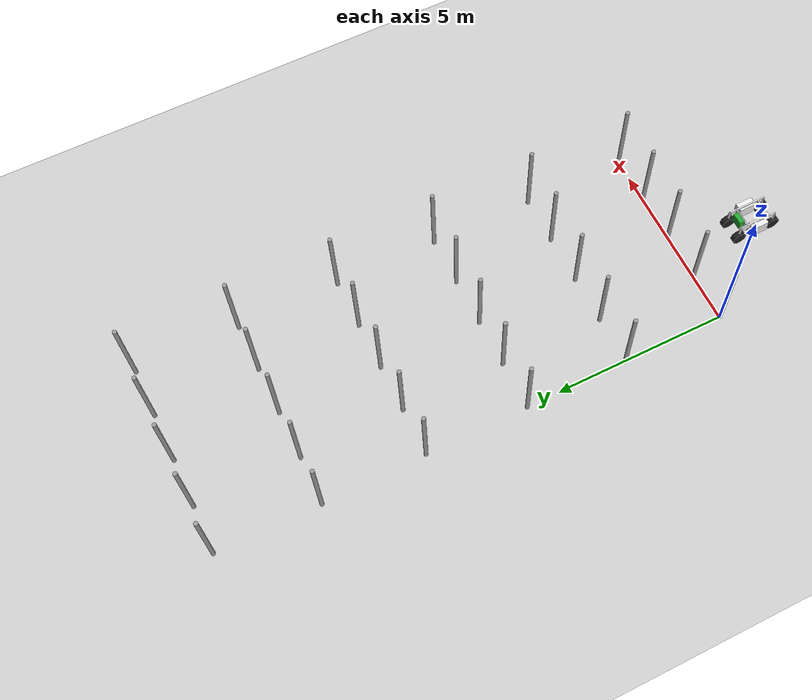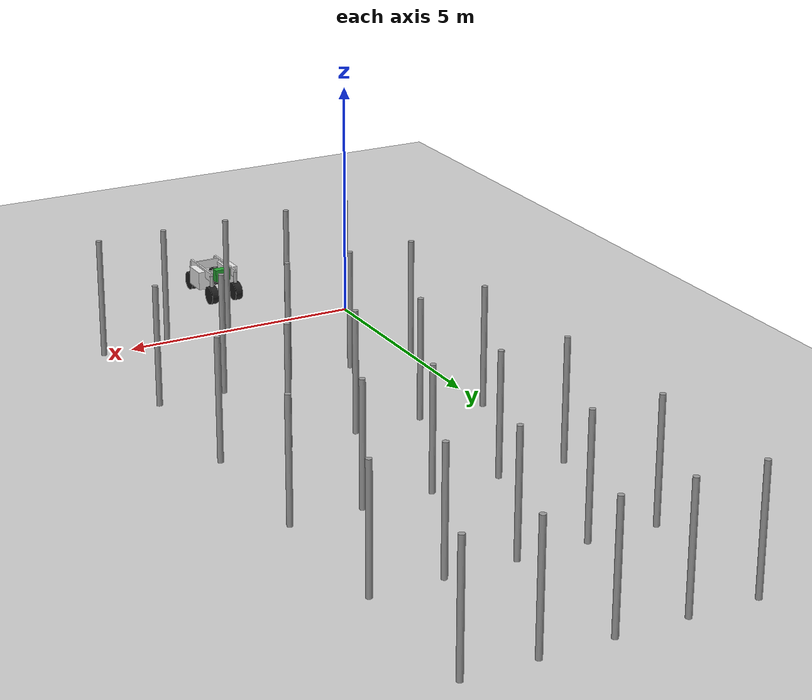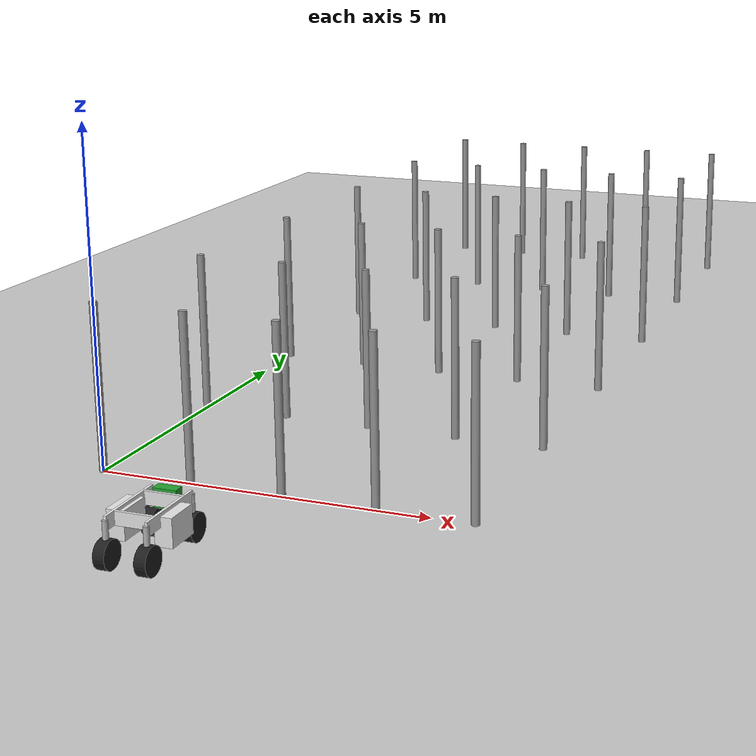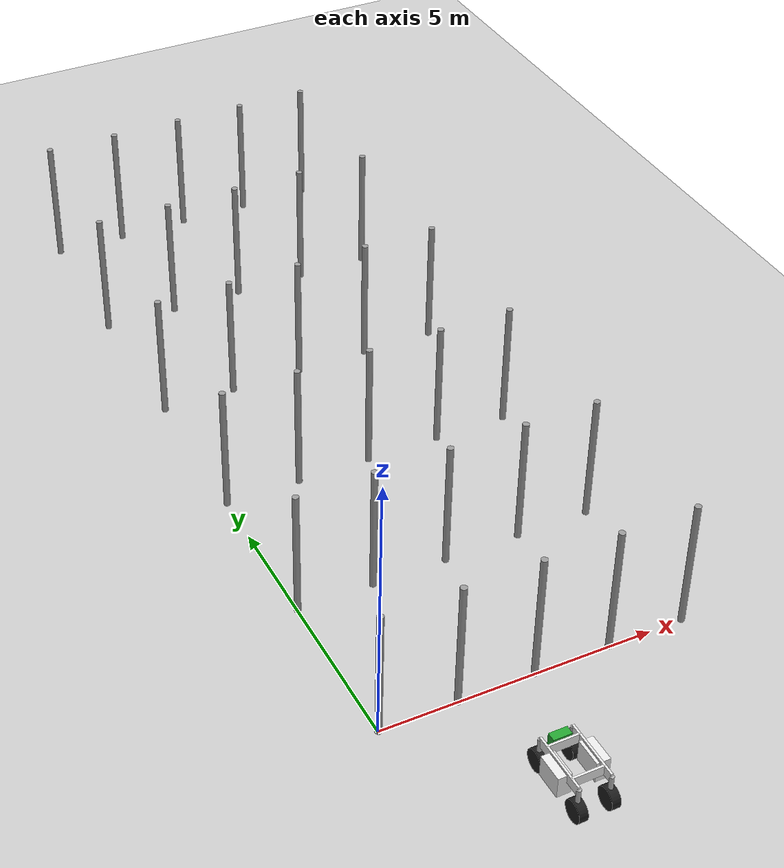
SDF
<sdf version="1.6">
 <world name="default">
  <light name="sun" type="directional">
   <pose>0 0 10 0 -0 0</pose>
   <diffuse>0.8 0.8 0.8 1</diffuse>
   <specular>0.1 0.1 0.1 1</specular>
   <attenuation>
    <range>1000</range>
    <constant>0.9</constant>
    <linear>0.01</linear>
    <quadratic>0.001</quadratic>
   </attenuation>
   <direction>-0.5 0.5 -1</direction>
  </light>
  <model name="ground_plane">
   <static>1</static>
   <link name="link">
    <collision name="collision">
     <geometry><plane><normal>0 0 1</normal><size>100 100</size></plane></geometry>
     <surface><friction><ode><mu>100</mu><mu2>50</mu2></ode></friction></surface>
    </collision>
    <visual name="visual">
     <cast_shadows>0</cast_shadows>
     <geometry><plane><normal>0 0 1</normal><size>100 100</size></plane></geometry>
     <material>
      <script><uri>file://media/materials/scripts/gazebo.material</uri><name>Gazebo/Grey</name></script>
     </material>
    </visual>
   </link>
  </model>
  <gravity>0 0 -9.8</gravity>
  <magnetic_field>6e-06 2.3e-05 -4.2e-05</magnetic_field>
  <atmosphere type="adiabatic"/>
  <physics name="default_physics" default="0" type="ode">
   <max_step_size>0.001</max_step_size>
   <real_time_factor>1</real_time_factor>
   <real_time_update_rate>1000</real_time_update_rate>
  </physics>
  <scene><ambient>0.4 0.4 0.4 1</ambient><background>0.7 0.7 0.7 1</background><shadows>1</shadows></scene>
  <spherical_coordinates>
   <surface_model>EARTH_WGS84</surface_model>
   <latitude_deg>0</latitude_deg>
   <longitude_deg>0</longitude_deg>
   <elevation>0</elevation>
   <heading_deg>0</heading_deg>
  </spherical_coordinates>
  <model name="pole_8">
   <link name="link_0">
    <inertial>
     <mass>0.0364582</mass>
     <inertia>
      <ixx>0.00312124</ixx>
      <ixy>0</ixy>
      <ixz>0</ixz>
      <iyy>0.00312124</iyy>
      <iyz>0</iyz>
      <izz>0.00016615</izz>
     </inertia>
    </inertial>
    <visual name="visual">
     <geometry><cylinder><radius>0.06</radius><length>2.5</length></cylinder></geometry>
     <material>
      <lighting>1</lighting>
      <script><uri>file://media/materials/scripts/gazebo.material</uri><name>Gazebo/Grey</name></script>
      <ambient>0.3 0.3 0.3 1</ambient>
      <diffuse>0.7 0.7 0.7 1</diffuse>
      <specular>0.01 0.01 0.01 1</specular>
      <emissive>0 0 0 1</emissive>
      <shader type="vertex"><normal_map>__default__</normal_map></shader>
     </material>
    </visual>
    <collision name="collision">
     <geometry><cylinder><radius>0.06</radius><length>2.5</length></cylinder></geometry>
     <surface>
      <friction>
       <ode><mu>1</mu><mu2>1</mu2><fdir1>0 0 0</fdir1><slip1>0</slip1><slip2>0</slip2></ode>
       <torsional>
        <coefficient>1</coefficient>
        <patch_radius>0</patch_radius>
        <surface_radius>0</surface_radius>
        <use_patch_radius>1</use_patch_radius>
        <ode><slip>0</slip></ode>
       </torsional>
      </friction>
      <bounce><restitution_coefficient>0</restitution_coefficient><threshold>1e+06</threshold></bounce>
      <contact>
       <collide_without_contact>0</collide_without_contact>
       <collide_without_contact_bitmask>1</collide_without_contact_bitmask>
       <collide_bitmask>1</collide_bitmask>
       <ode>
        <soft_cfm>0</soft_cfm>
        <soft_erp>0.2</soft_erp>
        <kp>1e+13</kp>
        <kd>1</kd>
        <max_vel>0.01</max_vel>
        <min_depth>0</min_depth>
       </ode>
       <bullet>
        <split_impulse>1</split_impulse>
        <split_impulse_penetration_threshold>-0.01</split_impulse_penetration_threshold>
        <soft_cfm>0</soft_cfm>
        <soft_erp>0.2</soft_erp>
        <kp>1e+13</kp>
        <kd>1</kd>
       </bullet>
      </contact>
     </surface>
    </collision>
   </link>
   <static>0</static>
   <pose>1.40421 0.001404 1.25 0 1e-06 -0.018336</pose>
  </model>
  <model name="pole_9">
   <link name="link_0">
    <inertial>
     <mass>0.0364582</mass>
     <inertia>
      <ixx>0.00312124</ixx>
      <ixy>0</ixy>
      <ixz>0</ixz>
      <iyy>0.00312124</iyy>
      <iyz>0</iyz>
      <izz>0.00016615</izz>
     </inertia>
    </inertial>
    <visual name="visual">
     <geometry><cylinder><radius>0.06</radius><length>2.5</length></cylinder></geometry>
     <material>
      <lighting>1</lighting>
      <script><uri>file://media/materials/scripts/gazebo.material</uri><name>Gazebo/Grey</name></script>
      <ambient>0.3 0.3 0.3 1</ambient>
      <diffuse>0.7 0.7 0.7 1</diffuse>
      <specular>0.01 0.01 0.01 1</specular>
      <emissive>0 0 0 1</emissive>
      <shader type="vertex"><normal_map>__default__</normal_map></shader>
     </material>
    </visual>
    <collision name="collision">
     <geometry><cylinder><radius>0.06</radius><length>2.5</length></cylinder></geometry>
     <surface>
      <friction>
       <ode><mu>1</mu><mu2>1</mu2><fdir1>0 0 0</fdir1><slip1>0</slip1><slip2>0</slip2></ode>
       <torsional>
        <coefficient>1</coefficient>
        <patch_radius>0</patch_radius>
        <surface_radius>0</surface_radius>
        <use_patch_radius>1</use_patch_radius>
        <ode><slip>0</slip></ode>
       </torsional>
      </friction>
      <bounce><restitution_coefficient>0</restitution_coefficient><threshold>1e+06</threshold></bounce>
      <contact>
       <collide_without_contact>0</collide_without_contact>
       <collide_without_contact_bitmask>1</collide_without_contact_bitmask>
       <collide_bitmask>1</collide_bitmask>
       <ode>
        <soft_cfm>0</soft_cfm>
        <soft_erp>0.2</soft_erp>
        <kp>1e+13</kp>
        <kd>1</kd>
        <max_vel>0.01</max_vel>
        <min_depth>0</min_depth>
       </ode>
       <bullet>
        <split_impulse>1</split_impulse>
        <split_impulse_penetration_threshold>-0.01</split_impulse_penetration_threshold>
        <soft_cfm>0</soft_cfm>
        <soft_erp>0.2</soft_erp>
        <kp>1e+13</kp>
        <kd>1</kd>
       </bullet>
      </contact>
     </surface>
    </collision>
   </link>
   <static>0</static>
   <pose>2.80801 0.0015 1.25 -1e-06 -1e-06 -0.036118</pose>
  </model>
  <model name="pole_10">
   <link name="link_0">
    <inertial>
     <mass>0.0364582</mass>
     <inertia>
      <ixx>0.00312124</ixx>
      <ixy>0</ixy>
      <ixz>0</ixz>
      <iyy>0.00312124</iyy>
      <iyz>0</iyz>
      <izz>0.00016615</izz>
     </inertia>
    </inertial>
    <visual name="visual">
     <geometry><cylinder><radius>0.06</radius><length>2.5</length></cylinder></geometry>
     <material>
      <lighting>1</lighting>
      <script><uri>file://media/materials/scripts/gazebo.material</uri><name>Gazebo/Grey</name></script>
      <ambient>0.3 0.3 0.3 1</ambient>
      <diffuse>0.7 0.7 0.7 1</diffuse>
      <specular>0.01 0.01 0.01 1</specular>
      <emissive>0 0 0 1</emissive>
      <shader type="vertex"><normal_map>__default__</normal_map></shader>
     </material>
    </visual>
    <collision name="collision">
     <geometry><cylinder><radius>0.06</radius><length>2.5</length></cylinder></geometry>
     <surface>
      <friction>
       <ode><mu>1</mu><mu2>1</mu2><fdir1>0 0 0</fdir1><slip1>0</slip1><slip2>0</slip2></ode>
       <torsional>
        <coefficient>1</coefficient>
        <patch_radius>0</patch_radius>
        <surface_radius>0</surface_radius>
        <use_patch_radius>1</use_patch_radius>
        <ode><slip>0</slip></ode>
       </torsional>
      </friction>
      <bounce><restitution_coefficient>0</restitution_coefficient><threshold>1e+06</threshold></bounce>
      <contact>
       <collide_without_contact>0</collide_without_contact>
       <collide_without_contact_bitmask>1</collide_without_contact_bitmask>
       <collide_bitmask>1</collide_bitmask>
       <ode>
        <soft_cfm>0</soft_cfm>
        <soft_erp>0.2</soft_erp>
        <kp>1e+13</kp>
        <kd>1</kd>
        <max_vel>0.01</max_vel>
        <min_depth>0</min_depth>
       </ode>
       <bullet>
        <split_impulse>1</split_impulse>
        <split_impulse_penetration_threshold>-0.01</split_impulse_penetration_threshold>
        <soft_cfm>0</soft_cfm>
        <soft_erp>0.2</soft_erp>
        <kp>1e+13</kp>
        <kd>1</kd>
       </bullet>
      </contact>
     </surface>
    </collision>
   </link>
   <static>0</static>
   <pose>4.20395 0.00148 1.25 1e-06 4e-06 -0.019904</pose>
  </model>
  <model name="pole_11">
   <link name="link_0">
    <inertial>
     <mass>0.0364582</mass>
     <inertia>
      <ixx>0.00312124</ixx>
      <ixy>0</ixy>
      <ixz>0</ixz>
      <iyy>0.00312124</iyy>
      <iyz>0</iyz>
      <izz>0.00016615</izz>
     </inertia>
    </inertial>
    <visual name="visual">
     <geometry><cylinder><radius>0.06</radius><length>2.5</length></cylinder></geometry>
     <material>
      <lighting>1</lighting>
      <script><uri>file://media/materials/scripts/gazebo.material</uri><name>Gazebo/Grey</name></script>
      <ambient>0.3 0.3 0.3 1</ambient>
      <diffuse>0.7 0.7 0.7 1</diffuse>
      <specular>0.01 0.01 0.01 1</specular>
      <emissive>0 0 0 1</emissive>
      <shader type="vertex"><normal_map>__default__</normal_map></shader>
     </material>
    </visual>
    <collision name="collision">
     <geometry><cylinder><radius>0.06</radius><length>2.5</length></cylinder></geometry>
     <surface>
      <friction>
       <ode><mu>1</mu><mu2>1</mu2><fdir1>0 0 0</fdir1><slip1>0</slip1><slip2>0</slip2></ode>
       <torsional>
        <coefficient>1</coefficient>
        <patch_radius>0</patch_radius>
        <surface_radius>0</surface_radius>
        <use_patch_radius>1</use_patch_radius>
        <ode><slip>0</slip></ode>
       </torsional>
      </friction>
      <bounce><restitution_coefficient>0</restitution_coefficient><threshold>1e+06</threshold></bounce>
      <contact>
       <collide_without_contact>0</collide_without_contact>
       <collide_without_contact_bitmask>1</collide_without_contact_bitmask>
       <collide_bitmask>1</collide_bitmask>
       <ode>
        <soft_cfm>0</soft_cfm>
        <soft_erp>0.2</soft_erp>
        <kp>1e+13</kp>
        <kd>1</kd>
        <max_vel>0.01</max_vel>
        <min_depth>0</min_depth>
       </ode>
       <bullet>
        <split_impulse>1</split_impulse>
        <split_impulse_penetration_threshold>-0.01</split_impulse_penetration_threshold>
        <soft_cfm>0</soft_cfm>
        <soft_erp>0.2</soft_erp>
        <kp>1e+13</kp>
        <kd>1</kd>
       </bullet>
      </contact>
     </surface>
    </collision>
   </link>
   <static>0</static>
   <pose>5.61622 0.00124 1.25 -1e-06 -1e-06 -0.019713</pose>
  </model>
  <model name="pole_11_clone">
   <link name="link_0">
    <inertial>
     <mass>0.0364582</mass>
     <inertia>
      <ixx>0.00312124</ixx>
      <ixy>0</ixy>
      <ixz>0</ixz>
      <iyy>0.00312124</iyy>
      <iyz>0</iyz>
      <izz>0.00016615</izz>
     </inertia>
    </inertial>
    <visual name="visual">
     <geometry><cylinder><radius>0.06</radius><length>2.5</length></cylinder></geometry>
     <material>
      <lighting>1</lighting>
      <script><uri>file://media/materials/scripts/gazebo.material</uri><name>Gazebo/Grey</name></script>
      <ambient>0.3 0.3 0.3 1</ambient>
      <diffuse>0.7 0.7 0.7 1</diffuse>
      <specular>0.01 0.01 0.01 1</specular>
      <emissive>0 0 0 1</emissive>
      <shader type="vertex"><normal_map>__default__</normal_map></shader>
     </material>
    </visual>
    <collision name="collision">
     <geometry><cylinder><radius>0.06</radius><length>2.5</length></cylinder></geometry>
     <surface>
      <friction>
       <ode><mu>1</mu><mu2>1</mu2><fdir1>0 0 0</fdir1><slip1>0</slip1><slip2>0</slip2></ode>
       <torsional>
        <coefficient>1</coefficient>
        <patch_radius>0</patch_radius>
        <surface_radius>0</surface_radius>
        <use_patch_radius>1</use_patch_radius>
        <ode><slip>0</slip></ode>
       </torsional>
      </friction>
      <bounce><restitution_coefficient>0</restitution_coefficient><threshold>1e+06</threshold></bounce>
      <contact>
       <collide_without_contact>0</collide_without_contact>
       <collide_without_contact_bitmask>1</collide_without_contact_bitmask>
       <collide_bitmask>1</collide_bitmask>
       <ode>
        <soft_cfm>0</soft_cfm>
        <soft_erp>0.2</soft_erp>
        <kp>1e+13</kp>
        <kd>1</kd>
        <max_vel>0.01</max_vel>
        <min_depth>0</min_depth>
       </ode>
       <bullet>
        <split_impulse>1</split_impulse>
        <split_impulse_penetration_threshold>-0.01</split_impulse_penetration_threshold>
        <soft_cfm>0</soft_cfm>
        <soft_erp>0.2</soft_erp>
        <kp>1e+13</kp>
        <kd>1</kd>
       </bullet>
      </contact>
     </surface>
    </collision>
   </link>
   <static>0</static>
   <pose>0.000229 2.98148 1.25 -1e-06 1e-06 -0.018464</pose>
  </model>
  <model name="pole">
   <link name="link_0">
    <inertial>
     <mass>0.0364582</mass>
     <inertia>
      <ixx>0.00312124</ixx>
      <ixy>0</ixy>
      <ixz>0</ixz>
      <iyy>0.00312124</iyy>
      <iyz>0</iyz>
      <izz>0.00016615</izz>
     </inertia>
    </inertial>
    <visual name="visual">
     <geometry><cylinder><radius>0.06</radius><length>2.5</length></cylinder></geometry>
     <material>
      <lighting>1</lighting>
      <script><uri>file://media/materials/scripts/gazebo.material</uri><name>Gazebo/Grey</name></script>
      <ambient>0.3 0.3 0.3 1</ambient>
      <diffuse>0.7 0.7 0.7 1</diffuse>
      <specular>0.01 0.01 0.01 1</specular>
      <emissive>0 0 0 1</emissive>
      <shader type="vertex"><normal_map>__default__</normal_map></shader>
     </material>
    </visual>
    <collision name="collision">
     <geometry><cylinder><radius>0.06</radius><length>2.5</length></cylinder></geometry>
     <surface>
      <friction>
       <ode><mu>1</mu><mu2>1</mu2><fdir1>0 0 0</fdir1><slip1>0</slip1><slip2>0</slip2></ode>
       <torsional>
        <coefficient>1</coefficient>
        <patch_radius>0</patch_radius>
        <surface_radius>0</surface_radius>
        <use_patch_radius>1</use_patch_radius>
        <ode><slip>0</slip></ode>
       </torsional>
      </friction>
      <bounce><restitution_coefficient>0</restitution_coefficient><threshold>1e+06</threshold></bounce>
      <contact>
       <collide_without_contact>0</collide_without_contact>
       <collide_without_contact_bitmask>1</collide_without_contact_bitmask>
       <collide_bitmask>1</collide_bitmask>
       <ode>
        <soft_cfm>0</soft_cfm>
        <soft_erp>0.2</soft_erp>
        <kp>1e+13</kp>
        <kd>1</kd>
        <max_vel>0.01</max_vel>
        <min_depth>0</min_depth>
       </ode>
       <bullet>
        <split_impulse>1</split_impulse>
        <split_impulse_penetration_threshold>-0.01</split_impulse_penetration_threshold>
        <soft_cfm>0</soft_cfm>
        <soft_erp>0.2</soft_erp>
        <kp>1e+13</kp>
        <kd>1</kd>
       </bullet>
      </contact>
     </surface>
    </collision>
   </link>
   <static>0</static>
   <pose>0.006679 5.96129 1.24999 -0 1e-06 -0.013434</pose>
  </model>
  <model name="pole_0">
   <link name="link_0">
    <inertial>
     <mass>0.0364582</mass>
     <inertia>
      <ixx>0.00312124</ixx>
      <ixy>0</ixy>
      <ixz>0</ixz>
      <iyy>0.00312124</iyy>
      <iyz>0</iyz>
      <izz>0.00016615</izz>
     </inertia>
    </inertial>
    <visual name="visual">
     <geometry><cylinder><radius>0.06</radius><length>2.5</length></cylinder></geometry>
     <material>
      <lighting>1</lighting>
      <script><uri>file://media/materials/scripts/gazebo.material</uri><name>Gazebo/Grey</name></script>
      <ambient>0.3 0.3 0.3 1</ambient>
      <diffuse>0.7 0.7 0.7 1</diffuse>
      <specular>0.01 0.01 0.01 1</specular>
      <emissive>0 0 0 1</emissive>
      <shader type="vertex"><normal_map>__default__</normal_map></shader>
     </material>
    </visual>
    <collision name="collision">
     <geometry><cylinder><radius>0.06</radius><length>2.5</length></cylinder></geometry>
     <surface>
      <friction>
       <ode><mu>1</mu><mu2>1</mu2><fdir1>0 0 0</fdir1><slip1>0</slip1><slip2>0</slip2></ode>
       <torsional>
        <coefficient>1</coefficient>
        <patch_radius>0</patch_radius>
        <surface_radius>0</surface_radius>
        <use_patch_radius>1</use_patch_radius>
        <ode><slip>0</slip></ode>
       </torsional>
      </friction>
      <bounce><restitution_coefficient>0</restitution_coefficient><threshold>1e+06</threshold></bounce>
      <contact>
       <collide_without_contact>0</collide_without_contact>
       <collide_without_contact_bitmask>1</collide_without_contact_bitmask>
       <collide_bitmask>1</collide_bitmask>
       <ode>
        <soft_cfm>0</soft_cfm>
        <soft_erp>0.2</soft_erp>
        <kp>1e+13</kp>
        <kd>1</kd>
        <max_vel>0.01</max_vel>
        <min_depth>0</min_depth>
       </ode>
       <bullet>
        <split_impulse>1</split_impulse>
        <split_impulse_penetration_threshold>-0.01</split_impulse_penetration_threshold>
        <soft_cfm>0</soft_cfm>
        <soft_erp>0.2</soft_erp>
        <kp>1e+13</kp>
        <kd>1</kd>
       </bullet>
      </contact>
     </surface>
    </collision>
   </link>
   <static>0</static>
   <pose>0.013487 8.9413 1.25 1e-06 3e-06 -0.016282</pose>
  </model>
  <model name="pole_1">
   <link name="link_0">
    <inertial>
     <mass>0.0364582</mass>
     <inertia>
      <ixx>0.00312124</ixx>
      <ixy>0</ixy>
      <ixz>0</ixz>
      <iyy>0.00312124</iyy>
      <iyz>0</iyz>
      <izz>0.00016615</izz>
     </inertia>
    </inertial>
    <visual name="visual">
     <geometry><cylinder><radius>0.06</radius><length>2.5</length></cylinder></geometry>
     <material>
      <lighting>1</lighting>
      <script><uri>file://media/materials/scripts/gazebo.material</uri><name>Gazebo/Grey</name></script>
      <ambient>0.3 0.3 0.3 1</ambient>
      <diffuse>0.7 0.7 0.7 1</diffuse>
      <specular>0.01 0.01 0.01 1</specular>
      <emissive>0 0 0 1</emissive>
      <shader type="vertex"><normal_map>__default__</normal_map></shader>
     </material>
    </visual>
    <collision name="collision">
     <geometry><cylinder><radius>0.06</radius><length>2.5</length></cylinder></geometry>
     <surface>
      <friction>
       <ode><mu>1</mu><mu2>1</mu2><fdir1>0 0 0</fdir1><slip1>0</slip1><slip2>0</slip2></ode>
       <torsional>
        <coefficient>1</coefficient>
        <patch_radius>0</patch_radius>
        <surface_radius>0</surface_radius>
        <use_patch_radius>1</use_patch_radius>
        <ode><slip>0</slip></ode>
       </torsional>
      </friction>
      <bounce><restitution_coefficient>0</restitution_coefficient><threshold>1e+06</threshold></bounce>
      <contact>
       <collide_without_contact>0</collide_without_contact>
       <collide_without_contact_bitmask>1</collide_without_contact_bitmask>
       <collide_bitmask>1</collide_bitmask>
       <ode>
        <soft_cfm>0</soft_cfm>
        <soft_erp>0.2</soft_erp>
        <kp>1e+13</kp>
        <kd>1</kd>
        <max_vel>0.01</max_vel>
        <min_depth>0</min_depth>
       </ode>
       <bullet>
        <split_impulse>1</split_impulse>
        <split_impulse_penetration_threshold>-0.01</split_impulse_penetration_threshold>
        <soft_cfm>0</soft_cfm>
        <soft_erp>0.2</soft_erp>
        <kp>1e+13</kp>
        <kd>1</kd>
       </bullet>
      </contact>
     </surface>
    </collision>
   </link>
   <static>0</static>
   <pose>-0.008122 11.9213 1.24999 -0 2e-06 -0.017959</pose>
  </model>
  <model name="pole_2">
   <link name="link_0">
    <inertial>
     <mass>0.0364582</mass>
     <inertia>
      <ixx>0.00312124</ixx>
      <ixy>0</ixy>
      <ixz>0</ixz>
      <iyy>0.00312124</iyy>
      <iyz>0</iyz>
      <izz>0.00016615</izz>
     </inertia>
    </inertial>
    <visual name="visual">
     <geometry><cylinder><radius>0.06</radius><length>2.5</length></cylinder></geometry>
     <material>
      <lighting>1</lighting>
      <script><uri>file://media/materials/scripts/gazebo.material</uri><name>Gazebo/Grey</name></script>
      <ambient>0.3 0.3 0.3 1</ambient>
      <diffuse>0.7 0.7 0.7 1</diffuse>
      <specular>0.01 0.01 0.01 1</specular>
      <emissive>0 0 0 1</emissive>
      <shader type="vertex"><normal_map>__default__</normal_map></shader>
     </material>
    </visual>
    <collision name="collision">
     <geometry><cylinder><radius>0.06</radius><length>2.5</length></cylinder></geometry>
     <surface>
      <friction>
       <ode><mu>1</mu><mu2>1</mu2><fdir1>0 0 0</fdir1><slip1>0</slip1><slip2>0</slip2></ode>
       <torsional>
        <coefficient>1</coefficient>
        <patch_radius>0</patch_radius>
        <surface_radius>0</surface_radius>
        <use_patch_radius>1</use_patch_radius>
        <ode><slip>0</slip></ode>
       </torsional>
      </friction>
      <bounce><restitution_coefficient>0</restitution_coefficient><threshold>1e+06</threshold></bounce>
      <contact>
       <collide_without_contact>0</collide_without_contact>
       <collide_without_contact_bitmask>1</collide_without_contact_bitmask>
       <collide_bitmask>1</collide_bitmask>
       <ode>
        <soft_cfm>0</soft_cfm>
        <soft_erp>0.2</soft_erp>
        <kp>1e+13</kp>
        <kd>1</kd>
        <max_vel>0.01</max_vel>
        <min_depth>0</min_depth>
       </ode>
       <bullet>
        <split_impulse>1</split_impulse>
        <split_impulse_penetration_threshold>-0.01</split_impulse_penetration_threshold>
        <soft_cfm>0</soft_cfm>
        <soft_erp>0.2</soft_erp>
        <kp>1e+13</kp>
        <kd>1</kd>
       </bullet>
      </contact>
     </surface>
    </collision>
   </link>
   <static>0</static>
   <pose>0.027547 14.8942 1.25 -1e-06 1e-06 0.219671</pose>
  </model>
  <model name="pole_3">
   <link name="link_0">
    <inertial>
     <mass>0.0364582</mass>
     <inertia>
      <ixx>0.00312124</ixx>
      <ixy>0</ixy>
      <ixz>0</ixz>
      <iyy>0.00312124</iyy>
      <iyz>0</iyz>
      <izz>0.00016615</izz>
     </inertia>
    </inertial>
    <visual name="visual">
     <geometry><cylinder><radius>0.06</radius><length>2.5</length></cylinder></geometry>
     <material>
      <lighting>1</lighting>
      <script><uri>file://media/materials/scripts/gazebo.material</uri><name>Gazebo/Grey</name></script>
      <ambient>0.3 0.3 0.3 1</ambient>
      <diffuse>0.7 0.7 0.7 1</diffuse>
      <specular>0.01 0.01 0.01 1</specular>
      <emissive>0 0 0 1</emissive>
      <shader type="vertex"><normal_map>__default__</normal_map></shader>
     </material>
    </visual>
    <collision name="collision">
     <geometry><cylinder><radius>0.06</radius><length>2.5</length></cylinder></geometry>
     <surface>
      <friction>
       <ode><mu>1</mu><mu2>1</mu2><fdir1>0 0 0</fdir1><slip1>0</slip1><slip2>0</slip2></ode>
       <torsional>
        <coefficient>1</coefficient>
        <patch_radius>0</patch_radius>
        <surface_radius>0</surface_radius>
        <use_patch_radius>1</use_patch_radius>
        <ode><slip>0</slip></ode>
       </torsional>
      </friction>
      <bounce><restitution_coefficient>0</restitution_coefficient><threshold>1e+06</threshold></bounce>
      <contact>
       <collide_without_contact>0</collide_without_contact>
       <collide_without_contact_bitmask>1</collide_without_contact_bitmask>
       <collide_bitmask>1</collide_bitmask>
       <ode>
        <soft_cfm>0</soft_cfm>
        <soft_erp>0.2</soft_erp>
        <kp>1e+13</kp>
        <kd>1</kd>
        <max_vel>0.01</max_vel>
        <min_depth>0</min_depth>
       </ode>
       <bullet>
        <split_impulse>1</split_impulse>
        <split_impulse_penetration_threshold>-0.01</split_impulse_penetration_threshold>
        <soft_cfm>0</soft_cfm>
        <soft_erp>0.2</soft_erp>
        <kp>1e+13</kp>
        <kd>1</kd>
       </bullet>
      </contact>
     </surface>
    </collision>
   </link>
   <static>0</static>
   <pose>1.40471 2.98102 1.25 -0 2e-06 -0.012848</pose>
  </model>
  <model name="pole_5">
   <link name="link_0">
    <inertial>
     <mass>0.0364582</mass>
     <inertia>
      <ixx>0.00312124</ixx>
      <ixy>0</ixy>
      <ixz>0</ixz>
      <iyy>0.00312124</iyy>
      <iyz>0</iyz>
      <izz>0.00016615</izz>
     </inertia>
    </inertial>
    <visual name="visual">
     <geometry><cylinder><radius>0.06</radius><length>2.5</length></cylinder></geometry>
     <material>
      <lighting>1</lighting>
      <script><uri>file://media/materials/scripts/gazebo.material</uri><name>Gazebo/Grey</name></script>
      <ambient>0.3 0.3 0.3 1</ambient>
      <diffuse>0.7 0.7 0.7 1</diffuse>
      <specular>0.01 0.01 0.01 1</specular>
      <emissive>0 0 0 1</emissive>
      <shader type="vertex"><normal_map>__default__</normal_map></shader>
     </material>
    </visual>
    <collision name="collision">
     <geometry><cylinder><radius>0.06</radius><length>2.5</length></cylinder></geometry>
     <surface>
      <friction>
       <ode><mu>1</mu><mu2>1</mu2><fdir1>0 0 0</fdir1><slip1>0</slip1><slip2>0</slip2></ode>
       <torsional>
        <coefficient>1</coefficient>
        <patch_radius>0</patch_radius>
        <surface_radius>0</surface_radius>
        <use_patch_radius>1</use_patch_radius>
        <ode><slip>0</slip></ode>
       </torsional>
      </friction>
      <bounce><restitution_coefficient>0</restitution_coefficient><threshold>1e+06</threshold></bounce>
      <contact>
       <collide_without_contact>0</collide_without_contact>
       <collide_without_contact_bitmask>1</collide_without_contact_bitmask>
       <collide_bitmask>1</collide_bitmask>
       <ode>
        <soft_cfm>0</soft_cfm>
        <soft_erp>0.2</soft_erp>
        <kp>1e+13</kp>
        <kd>1</kd>
        <max_vel>0.01</max_vel>
        <min_depth>0</min_depth>
       </ode>
       <bullet>
        <split_impulse>1</split_impulse>
        <split_impulse_penetration_threshold>-0.01</split_impulse_penetration_threshold>
        <soft_cfm>0</soft_cfm>
        <soft_erp>0.2</soft_erp>
        <kp>1e+13</kp>
        <kd>1</kd>
       </bullet>
      </contact>
     </surface>
    </collision>
   </link>
   <static>0</static>
   <pose>2.79582 2.98103 1.24999 -1e-06 -1e-06 -0.013933</pose>
  </model>
  <model name="pole_6">
   <link name="link_0">
    <inertial>
     <mass>0.0364582</mass>
     <inertia>
      <ixx>0.00312124</ixx>
      <ixy>0</ixy>
      <ixz>0</ixz>
      <iyy>0.00312124</iyy>
      <iyz>0</iyz>
      <izz>0.00016615</izz>
     </inertia>
    </inertial>
    <visual name="visual">
     <geometry><cylinder><radius>0.06</radius><length>2.5</length></cylinder></geometry>
     <material>
      <lighting>1</lighting>
      <script><uri>file://media/materials/scripts/gazebo.material</uri><name>Gazebo/Grey</name></script>
      <ambient>0.3 0.3 0.3 1</ambient>
      <diffuse>0.7 0.7 0.7 1</diffuse>
      <specular>0.01 0.01 0.01 1</specular>
      <emissive>0 0 0 1</emissive>
      <shader type="vertex"><normal_map>__default__</normal_map></shader>
     </material>
    </visual>
    <collision name="collision">
     <geometry><cylinder><radius>0.06</radius><length>2.5</length></cylinder></geometry>
     <surface>
      <friction>
       <ode><mu>1</mu><mu2>1</mu2><fdir1>0 0 0</fdir1><slip1>0</slip1><slip2>0</slip2></ode>
       <torsional>
        <coefficient>1</coefficient>
        <patch_radius>0</patch_radius>
        <surface_radius>0</surface_radius>
        <use_patch_radius>1</use_patch_radius>
        <ode><slip>0</slip></ode>
       </torsional>
      </friction>
      <bounce><restitution_coefficient>0</restitution_coefficient><threshold>1e+06</threshold></bounce>
      <contact>
       <collide_without_contact>0</collide_without_contact>
       <collide_without_contact_bitmask>1</collide_without_contact_bitmask>
       <collide_bitmask>1</collide_bitmask>
       <ode>
        <soft_cfm>0</soft_cfm>
        <soft_erp>0.2</soft_erp>
        <kp>1e+13</kp>
        <kd>1</kd>
        <max_vel>0.01</max_vel>
        <min_depth>0</min_depth>
       </ode>
       <bullet>
        <split_impulse>1</split_impulse>
        <split_impulse_penetration_threshold>-0.01</split_impulse_penetration_threshold>
        <soft_cfm>0</soft_cfm>
        <soft_erp>0.2</soft_erp>
        <kp>1e+13</kp>
        <kd>1</kd>
       </bullet>
      </contact>
     </surface>
    </collision>
   </link>
   <static>0</static>
   <pose>4.22239 2.98106 1.24999 -0 1e-06 -0.012593</pose>
  </model>
  <model name="pole_7">
   <link name="link_0">
    <inertial>
     <mass>0.0364582</mass>
     <inertia>
      <ixx>0.00312124</ixx>
      <ixy>0</ixy>
      <ixz>0</ixz>
      <iyy>0.00312124</iyy>
      <iyz>0</iyz>
      <izz>0.00016615</izz>
     </inertia>
    </inertial>
    <visual name="visual">
     <geometry><cylinder><radius>0.06</radius><length>2.5</length></cylinder></geometry>
     <material>
      <lighting>1</lighting>
      <script><uri>file://media/materials/scripts/gazebo.material</uri><name>Gazebo/Grey</name></script>
      <ambient>0.3 0.3 0.3 1</ambient>
      <diffuse>0.7 0.7 0.7 1</diffuse>
      <specular>0.01 0.01 0.01 1</specular>
      <emissive>0 0 0 1</emissive>
      <shader type="vertex"><normal_map>__default__</normal_map></shader>
     </material>
    </visual>
    <collision name="collision">
     <geometry><cylinder><radius>0.06</radius><length>2.5</length></cylinder></geometry>
     <surface>
      <friction>
       <ode><mu>1</mu><mu2>1</mu2><fdir1>0 0 0</fdir1><slip1>0</slip1><slip2>0</slip2></ode>
       <torsional>
        <coefficient>1</coefficient>
        <patch_radius>0</patch_radius>
        <surface_radius>0</surface_radius>
        <use_patch_radius>1</use_patch_radius>
        <ode><slip>0</slip></ode>
       </torsional>
      </friction>
      <bounce><restitution_coefficient>0</restitution_coefficient><threshold>1e+06</threshold></bounce>
      <contact>
       <collide_without_contact>0</collide_without_contact>
       <collide_without_contact_bitmask>1</collide_without_contact_bitmask>
       <collide_bitmask>1</collide_bitmask>
       <ode>
        <soft_cfm>0</soft_cfm>
        <soft_erp>0.2</soft_erp>
        <kp>1e+13</kp>
        <kd>1</kd>
        <max_vel>0.01</max_vel>
        <min_depth>0</min_depth>
       </ode>
       <bullet>
        <split_impulse>1</split_impulse>
        <split_impulse_penetration_threshold>-0.01</split_impulse_penetration_threshold>
        <soft_cfm>0</soft_cfm>
        <soft_erp>0.2</soft_erp>
        <kp>1e+13</kp>
        <kd>1</kd>
       </bullet>
      </contact>
     </surface>
    </collision>
   </link>
   <static>0</static>
   <pose>5.60731 2.98105 1.24999 0 0 -0.011558</pose>
  </model>
  <model name="pole_12">
   <link name="link_0">
    <inertial>
     <mass>0.0364582</mass>
     <inertia>
      <ixx>0.00312124</ixx>
      <ixy>0</ixy>
      <ixz>0</ixz>
      <iyy>0.00312124</iyy>
      <iyz>0</iyz>
      <izz>0.00016615</izz>
     </inertia>
    </inertial>
    <visual name="visual">
     <geometry><cylinder><radius>0.06</radius><length>2.5</length></cylinder></geometry>
     <material>
      <lighting>1</lighting>
      <script><uri>file://media/materials/scripts/gazebo.material</uri><name>Gazebo/Grey</name></script>
      <ambient>0.3 0.3 0.3 1</ambient>
      <diffuse>0.7 0.7 0.7 1</diffuse>
      <specular>0.01 0.01 0.01 1</specular>
      <emissive>0 0 0 1</emissive>
      <shader type="vertex"><normal_map>__default__</normal_map></shader>
     </material>
    </visual>
    <collision name="collision">
     <geometry><cylinder><radius>0.06</radius><length>2.5</length></cylinder></geometry>
     <surface>
      <friction>
       <ode><mu>1</mu><mu2>1</mu2><fdir1>0 0 0</fdir1><slip1>0</slip1><slip2>0</slip2></ode>
       <torsional>
        <coefficient>1</coefficient>
        <patch_radius>0</patch_radius>
        <surface_radius>0</surface_radius>
        <use_patch_radius>1</use_patch_radius>
        <ode><slip>0</slip></ode>
       </torsional>
      </friction>
      <bounce><restitution_coefficient>0</restitution_coefficient><threshold>1e+06</threshold></bounce>
      <contact>
       <collide_without_contact>0</collide_without_contact>
       <collide_without_contact_bitmask>1</collide_without_contact_bitmask>
       <collide_bitmask>1</collide_bitmask>
       <ode>
        <soft_cfm>0</soft_cfm>
        <soft_erp>0.2</soft_erp>
        <kp>1e+13</kp>
        <kd>1</kd>
        <max_vel>0.01</max_vel>
        <min_depth>0</min_depth>
       </ode>
       <bullet>
        <split_impulse>1</split_impulse>
        <split_impulse_penetration_threshold>-0.01</split_impulse_penetration_threshold>
        <soft_cfm>0</soft_cfm>
        <soft_erp>0.2</soft_erp>
        <kp>1e+13</kp>
        <kd>1</kd>
       </bullet>
      </contact>
     </surface>
    </collision>
   </link>
   <static>0</static>
   <pose>1.41361 5.96106 1.24999 0 1e-06 -0.011074</pose>
  </model>
  <model name="pole_13">
   <link name="link_0">
    <inertial>
     <mass>0.0364582</mass>
     <inertia>
      <ixx>0.00312124</ixx>
      <ixy>0</ixy>
      <ixz>0</ixz>
      <iyy>0.00312124</iyy>
      <iyz>0</iyz>
      <izz>0.00016615</izz>
     </inertia>
    </inertial>
    <visual name="visual">
     <geometry><cylinder><radius>0.06</radius><length>2.5</length></cylinder></geometry>
     <material>
      <lighting>1</lighting>
      <script><uri>file://media/materials/scripts/gazebo.material</uri><name>Gazebo/Grey</name></script>
      <ambient>0.3 0.3 0.3 1</ambient>
      <diffuse>0.7 0.7 0.7 1</diffuse>
      <specular>0.01 0.01 0.01 1</specular>
      <emissive>0 0 0 1</emissive>
      <shader type="vertex"><normal_map>__default__</normal_map></shader>
     </material>
    </visual>
    <collision name="collision">
     <geometry><cylinder><radius>0.06</radius><length>2.5</length></cylinder></geometry>
     <surface>
      <friction>
       <ode><mu>1</mu><mu2>1</mu2><fdir1>0 0 0</fdir1><slip1>0</slip1><slip2>0</slip2></ode>
       <torsional>
        <coefficient>1</coefficient>
        <patch_radius>0</patch_radius>
        <surface_radius>0</surface_radius>
        <use_patch_radius>1</use_patch_radius>
        <ode><slip>0</slip></ode>
       </torsional>
      </friction>
      <bounce><restitution_coefficient>0</restitution_coefficient><threshold>1e+06</threshold></bounce>
      <contact>
       <collide_without_contact>0</collide_without_contact>
       <collide_without_contact_bitmask>1</collide_without_contact_bitmask>
       <collide_bitmask>1</collide_bitmask>
       <ode>
        <soft_cfm>0</soft_cfm>
        <soft_erp>0.2</soft_erp>
        <kp>1e+13</kp>
        <kd>1</kd>
        <max_vel>0.01</max_vel>
        <min_depth>0</min_depth>
       </ode>
       <bullet>
        <split_impulse>1</split_impulse>
        <split_impulse_penetration_threshold>-0.01</split_impulse_penetration_threshold>
        <soft_cfm>0</soft_cfm>
        <soft_erp>0.2</soft_erp>
        <kp>1e+13</kp>
        <kd>1</kd>
       </bullet>
      </contact>
     </surface>
    </collision>
   </link>
   <static>0</static>
   <pose>2.80801 5.9611 1.24999 -0 2e-06 -0.010433</pose>
  </model>
  <model name="pole_14">
   <link name="link_0">
    <inertial>
     <mass>0.0364582</mass>
     <inertia>
      <ixx>0.00312124</ixx>
      <ixy>0</ixy>
      <ixz>0</ixz>
      <iyy>0.00312124</iyy>
      <iyz>0</iyz>
      <izz>0.00016615</izz>
     </inertia>
    </inertial>
    <visual name="visual">
     <geometry><cylinder><radius>0.06</radius><length>2.5</length></cylinder></geometry>
     <material>
      <lighting>1</lighting>
      <script><uri>file://media/materials/scripts/gazebo.material</uri><name>Gazebo/Grey</name></script>
      <ambient>0.3 0.3 0.3 1</ambient>
      <diffuse>0.7 0.7 0.7 1</diffuse>
      <specular>0.01 0.01 0.01 1</specular>
      <emissive>0 0 0 1</emissive>
      <shader type="vertex"><normal_map>__default__</normal_map></shader>
     </material>
    </visual>
    <collision name="collision">
     <geometry><cylinder><radius>0.06</radius><length>2.5</length></cylinder></geometry>
     <surface>
      <friction>
       <ode><mu>1</mu><mu2>1</mu2><fdir1>0 0 0</fdir1><slip1>0</slip1><slip2>0</slip2></ode>
       <torsional>
        <coefficient>1</coefficient>
        <patch_radius>0</patch_radius>
        <surface_radius>0</surface_radius>
        <use_patch_radius>1</use_patch_radius>
        <ode><slip>0</slip></ode>
       </torsional>
      </friction>
      <bounce><restitution_coefficient>0</restitution_coefficient><threshold>1e+06</threshold></bounce>
      <contact>
       <collide_without_contact>0</collide_without_contact>
       <collide_without_contact_bitmask>1</collide_without_contact_bitmask>
       <collide_bitmask>1</collide_bitmask>
       <ode>
        <soft_cfm>0</soft_cfm>
        <soft_erp>0.2</soft_erp>
        <kp>1e+13</kp>
        <kd>1</kd>
        <max_vel>0.01</max_vel>
        <min_depth>0</min_depth>
       </ode>
       <bullet>
        <split_impulse>1</split_impulse>
        <split_impulse_penetration_threshold>-0.01</split_impulse_penetration_threshold>
        <soft_cfm>0</soft_cfm>
        <soft_erp>0.2</soft_erp>
        <kp>1e+13</kp>
        <kd>1</kd>
       </bullet>
      </contact>
     </surface>
    </collision>
   </link>
   <static>0</static>
   <pose>4.2195 5.96104 1.24999 0 -1e-06 -0.009963</pose>
  </model>
  <model name="pole_15">
   <link name="link_0">
    <inertial>
     <mass>0.0364582</mass>
     <inertia>
      <ixx>0.00312124</ixx>
      <ixy>0</ixy>
      <ixz>0</ixz>
      <iyy>0.00312124</iyy>
      <iyz>0</iyz>
      <izz>0.00016615</izz>
     </inertia>
    </inertial>
    <visual name="visual">
     <geometry><cylinder><radius>0.06</radius><length>2.5</length></cylinder></geometry>
     <material>
      <lighting>1</lighting>
      <script><uri>file://media/materials/scripts/gazebo.material</uri><name>Gazebo/Grey</name></script>
      <ambient>0.3 0.3 0.3 1</ambient>
      <diffuse>0.7 0.7 0.7 1</diffuse>
      <specular>0.01 0.01 0.01 1</specular>
      <emissive>0 0 0 1</emissive>
      <shader type="vertex"><normal_map>__default__</normal_map></shader>
     </material>
    </visual>
    <collision name="collision">
     <geometry><cylinder><radius>0.06</radius><length>2.5</length></cylinder></geometry>
     <surface>
      <friction>
       <ode><mu>1</mu><mu2>1</mu2><fdir1>0 0 0</fdir1><slip1>0</slip1><slip2>0</slip2></ode>
       <torsional>
        <coefficient>1</coefficient>
        <patch_radius>0</patch_radius>
        <surface_radius>0</surface_radius>
        <use_patch_radius>1</use_patch_radius>
        <ode><slip>0</slip></ode>
       </torsional>
      </friction>
      <bounce><restitution_coefficient>0</restitution_coefficient><threshold>1e+06</threshold></bounce>
      <contact>
       <collide_without_contact>0</collide_without_contact>
       <collide_without_contact_bitmask>1</collide_without_contact_bitmask>
       <collide_bitmask>1</collide_bitmask>
       <ode>
        <soft_cfm>0</soft_cfm>
        <soft_erp>0.2</soft_erp>
        <kp>1e+13</kp>
        <kd>1</kd>
        <max_vel>0.01</max_vel>
        <min_depth>0</min_depth>
       </ode>
       <bullet>
        <split_impulse>1</split_impulse>
        <split_impulse_penetration_threshold>-0.01</split_impulse_penetration_threshold>
        <soft_cfm>0</soft_cfm>
        <soft_erp>0.2</soft_erp>
        <kp>1e+13</kp>
        <kd>1</kd>
       </bullet>
      </contact>
     </surface>
    </collision>
   </link>
   <static>0</static>
   <pose>5.6235 5.96101 1.25 0 1e-06 -0.010616</pose>
  </model>
  <model name="pole_16">
   <link name="link_0">
    <inertial>
     <mass>0.0364582</mass>
     <inertia>
      <ixx>0.00312124</ixx>
      <ixy>0</ixy>
      <ixz>0</ixz>
      <iyy>0.00312124</iyy>
      <iyz>0</iyz>
      <izz>0.00016615</izz>
     </inertia>
    </inertial>
    <visual name="visual">
     <geometry><cylinder><radius>0.06</radius><length>2.5</length></cylinder></geometry>
     <material>
      <lighting>1</lighting>
      <script><uri>file://media/materials/scripts/gazebo.material</uri><name>Gazebo/Grey</name></script>
      <ambient>0.3 0.3 0.3 1</ambient>
      <diffuse>0.7 0.7 0.7 1</diffuse>
      <specular>0.01 0.01 0.01 1</specular>
      <emissive>0 0 0 1</emissive>
      <shader type="vertex"><normal_map>__default__</normal_map></shader>
     </material>
    </visual>
    <collision name="collision">
     <geometry><cylinder><radius>0.06</radius><length>2.5</length></cylinder></geometry>
     <surface>
      <friction>
       <ode><mu>1</mu><mu2>1</mu2><fdir1>0 0 0</fdir1><slip1>0</slip1><slip2>0</slip2></ode>
       <torsional>
        <coefficient>1</coefficient>
        <patch_radius>0</patch_radius>
        <surface_radius>0</surface_radius>
        <use_patch_radius>1</use_patch_radius>
        <ode><slip>0</slip></ode>
       </torsional>
      </friction>
      <bounce><restitution_coefficient>0</restitution_coefficient><threshold>1e+06</threshold></bounce>
      <contact>
       <collide_without_contact>0</collide_without_contact>
       <collide_without_contact_bitmask>1</collide_without_contact_bitmask>
       <collide_bitmask>1</collide_bitmask>
       <ode>
        <soft_cfm>0</soft_cfm>
        <soft_erp>0.2</soft_erp>
        <kp>1e+13</kp>
        <kd>1</kd>
        <max_vel>0.01</max_vel>
        <min_depth>0</min_depth>
       </ode>
       <bullet>
        <split_impulse>1</split_impulse>
        <split_impulse_penetration_threshold>-0.01</split_impulse_penetration_threshold>
        <soft_cfm>0</soft_cfm>
        <soft_erp>0.2</soft_erp>
        <kp>1e+13</kp>
        <kd>1</kd>
       </bullet>
      </contact>
     </surface>
    </collision>
   </link>
   <static>0</static>
   <pose>1.4131 8.94056 1.24999 -1e-06 -0 -0.011505</pose>
  </model>
  <model name="pole_17">
   <link name="link_0">
    <inertial>
     <mass>0.0364582</mass>
     <inertia>
      <ixx>0.00312124</ixx>
      <ixy>0</ixy>
      <ixz>0</ixz>
      <iyy>0.00312124</iyy>
      <iyz>0</iyz>
      <izz>0.00016615</izz>
     </inertia>
    </inertial>
    <visual name="visual">
     <geometry><cylinder><radius>0.06</radius><length>2.5</length></cylinder></geometry>
     <material>
      <lighting>1</lighting>
      <script><uri>file://media/materials/scripts/gazebo.material</uri><name>Gazebo/Grey</name></script>
      <ambient>0.3 0.3 0.3 1</ambient>
      <diffuse>0.7 0.7 0.7 1</diffuse>
      <specular>0.01 0.01 0.01 1</specular>
      <emissive>0 0 0 1</emissive>
      <shader type="vertex"><normal_map>__default__</normal_map></shader>
     </material>
    </visual>
    <collision name="collision">
     <geometry><cylinder><radius>0.06</radius><length>2.5</length></cylinder></geometry>
     <surface>
      <friction>
       <ode><mu>1</mu><mu2>1</mu2><fdir1>0 0 0</fdir1><slip1>0</slip1><slip2>0</slip2></ode>
       <torsional>
        <coefficient>1</coefficient>
        <patch_radius>0</patch_radius>
        <surface_radius>0</surface_radius>
        <use_patch_radius>1</use_patch_radius>
        <ode><slip>0</slip></ode>
       </torsional>
      </friction>
      <bounce><restitution_coefficient>0</restitution_coefficient><threshold>1e+06</threshold></bounce>
      <contact>
       <collide_without_contact>0</collide_without_contact>
       <collide_without_contact_bitmask>1</collide_without_contact_bitmask>
       <collide_bitmask>1</collide_bitmask>
       <ode>
        <soft_cfm>0</soft_cfm>
        <soft_erp>0.2</soft_erp>
        <kp>1e+13</kp>
        <kd>1</kd>
        <max_vel>0.01</max_vel>
        <min_depth>0</min_depth>
       </ode>
       <bullet>
        <split_impulse>1</split_impulse>
        <split_impulse_penetration_threshold>-0.01</split_impulse_penetration_threshold>
        <soft_cfm>0</soft_cfm>
        <soft_erp>0.2</soft_erp>
        <kp>1e+13</kp>
        <kd>1</kd>
       </bullet>
      </contact>
     </surface>
    </collision>
   </link>
   <static>0</static>
   <pose>2.79984 8.94076 1.25 -1e-06 -2e-06 -0.007995</pose>
  </model>
  <model name="pole_18">
   <link name="link_0">
    <inertial>
     <mass>0.0364582</mass>
     <inertia>
      <ixx>0.00312124</ixx>
      <ixy>0</ixy>
      <ixz>0</ixz>
      <iyy>0.00312124</iyy>
      <iyz>0</iyz>
      <izz>0.00016615</izz>
     </inertia>
    </inertial>
    <visual name="visual">
     <geometry><cylinder><radius>0.06</radius><length>2.5</length></cylinder></geometry>
     <material>
      <lighting>1</lighting>
      <script><uri>file://media/materials/scripts/gazebo.material</uri><name>Gazebo/Grey</name></script>
      <ambient>0.3 0.3 0.3 1</ambient>
      <diffuse>0.7 0.7 0.7 1</diffuse>
      <specular>0.01 0.01 0.01 1</specular>
      <emissive>0 0 0 1</emissive>
      <shader type="vertex"><normal_map>__default__</normal_map></shader>
     </material>
    </visual>
    <collision name="collision">
     <geometry><cylinder><radius>0.06</radius><length>2.5</length></cylinder></geometry>
     <surface>
      <friction>
       <ode><mu>1</mu><mu2>1</mu2><fdir1>0 0 0</fdir1><slip1>0</slip1><slip2>0</slip2></ode>
       <torsional>
        <coefficient>1</coefficient>
        <patch_radius>0</patch_radius>
        <surface_radius>0</surface_radius>
        <use_patch_radius>1</use_patch_radius>
        <ode><slip>0</slip></ode>
       </torsional>
      </friction>
      <bounce><restitution_coefficient>0</restitution_coefficient><threshold>1e+06</threshold></bounce>
      <contact>
       <collide_without_contact>0</collide_without_contact>
       <collide_without_contact_bitmask>1</collide_without_contact_bitmask>
       <collide_bitmask>1</collide_bitmask>
       <ode>
        <soft_cfm>0</soft_cfm>
        <soft_erp>0.2</soft_erp>
        <kp>1e+13</kp>
        <kd>1</kd>
        <max_vel>0.01</max_vel>
        <min_depth>0</min_depth>
       </ode>
       <bullet>
        <split_impulse>1</split_impulse>
        <split_impulse_penetration_threshold>-0.01</split_impulse_penetration_threshold>
        <soft_cfm>0</soft_cfm>
        <soft_erp>0.2</soft_erp>
        <kp>1e+13</kp>
        <kd>1</kd>
       </bullet>
      </contact>
     </surface>
    </collision>
   </link>
   <static>0</static>
   <pose>4.20386 8.94064 1.24999 -1e-06 3e-06 -0.007315</pose>
  </model>
  <model name="pole_19">
   <link name="link_0">
    <inertial>
     <mass>0.0364582</mass>
     <inertia>
      <ixx>0.00312124</ixx>
      <ixy>0</ixy>
      <ixz>0</ixz>
      <iyy>0.00312124</iyy>
      <iyz>0</iyz>
      <izz>0.00016615</izz>
     </inertia>
    </inertial>
    <visual name="visual">
     <geometry><cylinder><radius>0.06</radius><length>2.5</length></cylinder></geometry>
     <material>
      <lighting>1</lighting>
      <script><uri>file://media/materials/scripts/gazebo.material</uri><name>Gazebo/Grey</name></script>
      <ambient>0.3 0.3 0.3 1</ambient>
      <diffuse>0.7 0.7 0.7 1</diffuse>
      <specular>0.01 0.01 0.01 1</specular>
      <emissive>0 0 0 1</emissive>
      <shader type="vertex"><normal_map>__default__</normal_map></shader>
     </material>
    </visual>
    <collision name="collision">
     <geometry><cylinder><radius>0.06</radius><length>2.5</length></cylinder></geometry>
     <surface>
      <friction>
       <ode><mu>1</mu><mu2>1</mu2><fdir1>0 0 0</fdir1><slip1>0</slip1><slip2>0</slip2></ode>
       <torsional>
        <coefficient>1</coefficient>
        <patch_radius>0</patch_radius>
        <surface_radius>0</surface_radius>
        <use_patch_radius>1</use_patch_radius>
        <ode><slip>0</slip></ode>
       </torsional>
      </friction>
      <bounce><restitution_coefficient>0</restitution_coefficient><threshold>1e+06</threshold></bounce>
      <contact>
       <collide_without_contact>0</collide_without_contact>
       <collide_without_contact_bitmask>1</collide_without_contact_bitmask>
       <collide_bitmask>1</collide_bitmask>
       <ode>
        <soft_cfm>0</soft_cfm>
        <soft_erp>0.2</soft_erp>
        <kp>1e+13</kp>
        <kd>1</kd>
        <max_vel>0.01</max_vel>
        <min_depth>0</min_depth>
       </ode>
       <bullet>
        <split_impulse>1</split_impulse>
        <split_impulse_penetration_threshold>-0.01</split_impulse_penetration_threshold>
        <soft_cfm>0</soft_cfm>
        <soft_erp>0.2</soft_erp>
        <kp>1e+13</kp>
        <kd>1</kd>
       </bullet>
      </contact>
     </surface>
    </collision>
   </link>
   <static>0</static>
   <pose>5.62932 8.94069 1.25 0 1e-06 -0.007692</pose>
  </model>
  <model name="pole_20">
   <link name="link_0">
    <inertial>
     <mass>0.0364582</mass>
     <inertia>
      <ixx>0.00312124</ixx>
      <ixy>0</ixy>
      <ixz>0</ixz>
      <iyy>0.00312124</iyy>
      <iyz>0</iyz>
      <izz>0.00016615</izz>
     </inertia>
    </inertial>
    <visual name="visual">
     <geometry><cylinder><radius>0.06</radius><length>2.5</length></cylinder></geometry>
     <material>
      <lighting>1</lighting>
      <script><uri>file://media/materials/scripts/gazebo.material</uri><name>Gazebo/Grey</name></script>
      <ambient>0.3 0.3 0.3 1</ambient>
      <diffuse>0.7 0.7 0.7 1</diffuse>
      <specular>0.01 0.01 0.01 1</specular>
      <emissive>0 0 0 1</emissive>
      <shader type="vertex"><normal_map>__default__</normal_map></shader>
     </material>
    </visual>
    <collision name="collision">
     <geometry><cylinder><radius>0.06</radius><length>2.5</length></cylinder></geometry>
     <surface>
      <friction>
       <ode><mu>1</mu><mu2>1</mu2><fdir1>0 0 0</fdir1><slip1>0</slip1><slip2>0</slip2></ode>
       <torsional>
        <coefficient>1</coefficient>
        <patch_radius>0</patch_radius>
        <surface_radius>0</surface_radius>
        <use_patch_radius>1</use_patch_radius>
        <ode><slip>0</slip></ode>
       </torsional>
      </friction>
      <bounce><restitution_coefficient>0</restitution_coefficient><threshold>1e+06</threshold></bounce>
      <contact>
       <collide_without_contact>0</collide_without_contact>
       <collide_without_contact_bitmask>1</collide_without_contact_bitmask>
       <collide_bitmask>1</collide_bitmask>
       <ode>
        <soft_cfm>0</soft_cfm>
        <soft_erp>0.2</soft_erp>
        <kp>1e+13</kp>
        <kd>1</kd>
        <max_vel>0.01</max_vel>
        <min_depth>0</min_depth>
       </ode>
       <bullet>
        <split_impulse>1</split_impulse>
        <split_impulse_penetration_threshold>-0.01</split_impulse_penetration_threshold>
        <soft_cfm>0</soft_cfm>
        <soft_erp>0.2</soft_erp>
        <kp>1e+13</kp>
        <kd>1</kd>
       </bullet>
      </contact>
     </surface>
    </collision>
   </link>
   <static>0</static>
   <pose>1.39577 11.9005 1.25 -1e-06 -0 -0.005165</pose>
  </model>
  <model name="pole_21">
   <link name="link_0">
    <inertial>
     <mass>0.0364582</mass>
     <inertia>
      <ixx>0.00312124</ixx>
      <ixy>0</ixy>
      <ixz>0</ixz>
      <iyy>0.00312124</iyy>
      <iyz>0</iyz>
      <izz>0.00016615</izz>
     </inertia>
    </inertial>
    <visual name="visual">
     <geometry><cylinder><radius>0.06</radius><length>2.5</length></cylinder></geometry>
     <material>
      <lighting>1</lighting>
      <script><uri>file://media/materials/scripts/gazebo.material</uri><name>Gazebo/Grey</name></script>
      <ambient>0.3 0.3 0.3 1</ambient>
      <diffuse>0.7 0.7 0.7 1</diffuse>
      <specular>0.01 0.01 0.01 1</specular>
      <emissive>0 0 0 1</emissive>
      <shader type="vertex"><normal_map>__default__</normal_map></shader>
     </material>
    </visual>
    <collision name="collision">
     <geometry><cylinder><radius>0.06</radius><length>2.5</length></cylinder></geometry>
     <surface>
      <friction>
       <ode><mu>1</mu><mu2>1</mu2><fdir1>0 0 0</fdir1><slip1>0</slip1><slip2>0</slip2></ode>
       <torsional>
        <coefficient>1</coefficient>
        <patch_radius>0</patch_radius>
        <surface_radius>0</surface_radius>
        <use_patch_radius>1</use_patch_radius>
        <ode><slip>0</slip></ode>
       </torsional>
      </friction>
      <bounce><restitution_coefficient>0</restitution_coefficient><threshold>1e+06</threshold></bounce>
      <contact>
       <collide_without_contact>0</collide_without_contact>
       <collide_without_contact_bitmask>1</collide_without_contact_bitmask>
       <collide_bitmask>1</collide_bitmask>
       <ode>
        <soft_cfm>0</soft_cfm>
        <soft_erp>0.2</soft_erp>
        <kp>1e+13</kp>
        <kd>1</kd>
        <max_vel>0.01</max_vel>
        <min_depth>0</min_depth>
       </ode>
       <bullet>
        <split_impulse>1</split_impulse>
        <split_impulse_penetration_threshold>-0.01</split_impulse_penetration_threshold>
        <soft_cfm>0</soft_cfm>
        <soft_erp>0.2</soft_erp>
        <kp>1e+13</kp>
        <kd>1</kd>
       </bullet>
      </contact>
     </surface>
    </collision>
   </link>
   <static>0</static>
   <pose>2.80779 11.901 1.25 0 0 -0.022297</pose>
  </model>
  <model name="pole_22">
   <link name="link_0">
    <inertial>
     <mass>0.0364582</mass>
     <inertia>
      <ixx>0.00312124</ixx>
      <ixy>0</ixy>
      <ixz>0</ixz>
      <iyy>0.00312124</iyy>
      <iyz>0</iyz>
      <izz>0.00016615</izz>
     </inertia>
    </inertial>
    <visual name="visual">
     <geometry><cylinder><radius>0.06</radius><length>2.5</length></cylinder></geometry>
     <material>
      <lighting>1</lighting>
      <script><uri>file://media/materials/scripts/gazebo.material</uri><name>Gazebo/Grey</name></script>
      <ambient>0.3 0.3 0.3 1</ambient>
      <diffuse>0.7 0.7 0.7 1</diffuse>
      <specular>0.01 0.01 0.01 1</specular>
      <emissive>0 0 0 1</emissive>
      <shader type="vertex"><normal_map>__default__</normal_map></shader>
     </material>
    </visual>
    <collision name="collision">
     <geometry><cylinder><radius>0.06</radius><length>2.5</length></cylinder></geometry>
     <surface>
      <friction>
       <ode><mu>1</mu><mu2>1</mu2><fdir1>0 0 0</fdir1><slip1>0</slip1><slip2>0</slip2></ode>
       <torsional>
        <coefficient>1</coefficient>
        <patch_radius>0</patch_radius>
        <surface_radius>0</surface_radius>
        <use_patch_radius>1</use_patch_radius>
        <ode><slip>0</slip></ode>
       </torsional>
      </friction>
      <bounce><restitution_coefficient>0</restitution_coefficient><threshold>1e+06</threshold></bounce>
      <contact>
       <collide_without_contact>0</collide_without_contact>
       <collide_without_contact_bitmask>1</collide_without_contact_bitmask>
       <collide_bitmask>1</collide_bitmask>
       <ode>
        <soft_cfm>0</soft_cfm>
        <soft_erp>0.2</soft_erp>
        <kp>1e+13</kp>
        <kd>1</kd>
        <max_vel>0.01</max_vel>
        <min_depth>0</min_depth>
       </ode>
       <bullet>
        <split_impulse>1</split_impulse>
        <split_impulse_penetration_threshold>-0.01</split_impulse_penetration_threshold>
        <soft_cfm>0</soft_cfm>
        <soft_erp>0.2</soft_erp>
        <kp>1e+13</kp>
        <kd>1</kd>
       </bullet>
      </contact>
     </surface>
    </collision>
   </link>
   <static>0</static>
   <pose>4.21208 11.9004 1.25 1e-06 -4e-06 -0.005319</pose>
  </model>
  <model name="pole_23">
   <link name="link_0">
    <inertial>
     <mass>0.0364582</mass>
     <inertia>
      <ixx>0.00312124</ixx>
      <ixy>0</ixy>
      <ixz>0</ixz>
      <iyy>0.00312124</iyy>
      <iyz>0</iyz>
      <izz>0.00016615</izz>
     </inertia>
    </inertial>
    <visual name="visual">
     <geometry><cylinder><radius>0.06</radius><length>2.5</length></cylinder></geometry>
     <material>
      <lighting>1</lighting>
      <script><uri>file://media/materials/scripts/gazebo.material</uri><name>Gazebo/Grey</name></script>
      <ambient>0.3 0.3 0.3 1</ambient>
      <diffuse>0.7 0.7 0.7 1</diffuse>
      <specular>0.01 0.01 0.01 1</specular>
      <emissive>0 0 0 1</emissive>
      <shader type="vertex"><normal_map>__default__</normal_map></shader>
     </material>
    </visual>
    <collision name="collision">
     <geometry><cylinder><radius>0.06</radius><length>2.5</length></cylinder></geometry>
     <surface>
      <friction>
       <ode><mu>1</mu><mu2>1</mu2><fdir1>0 0 0</fdir1><slip1>0</slip1><slip2>0</slip2></ode>
       <torsional>
        <coefficient>1</coefficient>
        <patch_radius>0</patch_radius>
        <surface_radius>0</surface_radius>
        <use_patch_radius>1</use_patch_radius>
        <ode><slip>0</slip></ode>
       </torsional>
      </friction>
      <bounce><restitution_coefficient>0</restitution_coefficient><threshold>1e+06</threshold></bounce>
      <contact>
       <collide_without_contact>0</collide_without_contact>
       <collide_without_contact_bitmask>1</collide_without_contact_bitmask>
       <collide_bitmask>1</collide_bitmask>
       <ode>
        <soft_cfm>0</soft_cfm>
        <soft_erp>0.2</soft_erp>
        <kp>1e+13</kp>
        <kd>1</kd>
        <max_vel>0.01</max_vel>
        <min_depth>0</min_depth>
       </ode>
       <bullet>
        <split_impulse>1</split_impulse>
        <split_impulse_penetration_threshold>-0.01</split_impulse_penetration_threshold>
        <soft_cfm>0</soft_cfm>
        <soft_erp>0.2</soft_erp>
        <kp>1e+13</kp>
        <kd>1</kd>
       </bullet>
      </contact>
     </surface>
    </collision>
   </link>
   <static>0</static>
   <pose>5.61606 11.9005 1.24999 0 1e-06 -0.004268</pose>
  </model>
  <model name="thorvald_ii">
   <link name="front_frame">
    <inertial>
     <pose>-0.486949 0 -0.042757 0 -0 0</pose>
     <mass>44.3428</mass>
     <inertia>
      <ixx>22.1052</ixx>
      <ixy>3.159</ixy>
      <ixz>4.75844</ixz>
      <iyy>21.4953</iyy>
      <iyz>7.54392</iyz>
      <izz>16.1935</izz>
     </inertia>
    </inertial>
    <collision name="front_frame_fixed_joint_lump__front_link_collision">
     <pose>-0.2 0 0 0 -0 0</pose>
     <geometry><box><size>0.04 0.57 0.19</size></box></geometry>
    </collision>
    <collision name="front_frame_fixed_joint_lump__frame_left_link_collision_1">
     <pose>-0.5475 0.285 0 0 -0 0</pose>
     <geometry><box><size>1.095 0.04 0.19</size></box></geometry>
    </collision>
    <collision name="front_frame_fixed_joint_lump__left_battery_link_collision_2">
     <pose>-0.5475 0.335 -0.15 0 -0 0</pose>
     <geometry><box><size>0.5 0.25 0.4</size></box></geometry>
    </collision>
    <collision name="front_frame_fixed_joint_lump__frame_right_link_collision_3">
     <pose>-0.5475 -0.285 0 0 -0 0</pose>
     <geometry><box><size>1.095 0.04 0.19</size></box></geometry>
    </collision>
    <collision name="front_frame_fixed_joint_lump__right_battery_link_collision_4">
     <pose>-0.5475 -0.335 -0.15 0 -0 0</pose>
     <geometry><box><size>0.5 0.25 0.4</size></box></geometry>
    </collision>
    <collision name="front_frame_fixed_joint_lump__sensor_box_link_collision_5">
     <pose>-0.1 0 0 0 -0 0</pose>
     <geometry><box><size>0.159 0.336 0.27</size></box></geometry>
    </collision>
    <collision name="front_frame_fixed_joint_lump__rear_link_collision_6">
     <pose>-0.895 0 0 0 -0 0</pose>
     <geometry><box><size>0.04 0.57 0.19</size></box></geometry>
    </collision>
    <visual name="front_frame_fixed_joint_lump__front_link_visual">
     <pose>-0.2 0 0 0 -0 0</pose>
     <geometry><box><size>0.04 0.57 0.19</size></box></geometry>
     <material>
      <script><name>Gazebo/White</name><uri>file://media/materials/scripts/gazebo.material</uri></script>
     </material>
    </visual>
    <visual name="front_frame_fixed_joint_lump__frame_left_link_visual_1">
     <pose>-0.5475 0.285 0 0 -0 0</pose>
     <geometry><box><size>1.095 0.04 0.19</size></box></geometry>
     <material>
      <script><name>Gazebo/White</name><uri>file://media/materials/scripts/gazebo.material</uri></script>
     </material>
    </visual>
    <visual name="front_frame_fixed_joint_lump__left_battery_link_visual_2">
     <pose>-0.5475 0.335 -0.15 0 -0 0</pose>
     <geometry><box><size>0.5 0.25 0.4</size></box></geometry>
     <material>
      <script><name>Gazebo/White</name><uri>file://media/materials/scripts/gazebo.material</uri></script>
     </material>
    </visual>
    <visual name="front_frame_fixed_joint_lump__frame_right_link_visual_3">
     <pose>-0.5475 -0.285 0 0 -0 0</pose>
     <geometry><box><size>1.095 0.04 0.19</size></box></geometry>
     <material>
      <script><name>Gazebo/White</name><uri>file://media/materials/scripts/gazebo.material</uri></script>
     </material>
    </visual>
    <visual name="front_frame_fixed_joint_lump__right_battery_link_visual_4">
     <pose>-0.5475 -0.335 -0.15 0 -0 0</pose>
     <geometry><box><size>0.5 0.25 0.4</size></box></geometry>
     <material>
      <script><name>Gazebo/White</name><uri>file://media/materials/scripts/gazebo.material</uri></script>
     </material>
    </visual>
    <visual name="front_frame_fixed_joint_lump__sensor_box_link_visual_5">
     <pose>-0.1 0 0 0 -0 0</pose>
     <geometry><box><size>0.159 0.336 0.27</size></box></geometry>
     <material>
      <script><name>Gazebo/Green</name><uri>file://media/materials/scripts/gazebo.material</uri></script>
     </material>
    </visual>
    <visual name="front_frame_fixed_joint_lump__rear_link_visual_6">
     <pose>-0.895 0 0 0 -0 0</pose>
     <geometry><box><size>0.04 0.57 0.19</size></box></geometry>
     <material>
      <script><name>Gazebo/White</name><uri>file://media/materials/scripts/gazebo.material</uri></script>
     </material>
    </visual>
   </link>
   <link name="front_left_leg">
    <pose>0 0.285 -0.2 0 -0 0</pose>
    <inertial>
     <mass>18.0411</mass>
     <inertia>
      <ixx>0.420701</ixx>
      <ixy>-0.0682293</ixy>
      <ixz>0.00112609</ixz>
      <iyy>0.140328</iyy>
      <iyz>0.0416406</iyz>
      <izz>0.371963</izz>
     </inertia>
    </inertial>
    <collision name="front_left_leg_collision">
     <geometry><cylinder><length>0.495</length><radius>0.04</radius></cylinder></geometry>
    </collision>
    <visual name="front_left_leg_visual">
     <geometry><cylinder><length>0.495</length><radius>0.04</radius></cylinder></geometry>
    </visual>
   </link>
   <joint name="steering2" type="revolute">
    <child>front_left_leg</child>
    <parent>front_frame</parent>
    <axis>
     <xyz>0 0 1</xyz>
     <limit><lower>-1e+16</lower><upper>1e+16</upper></limit>
     <dynamics><spring_reference>0</spring_reference><spring_stiffness>0</spring_stiffness></dynamics>
     <use_parent_model_frame>1</use_parent_model_frame>
    </axis>
   </joint>
   <link name="front_left_wheel">
    <pose>0 0.285 -0.4 -1.5708 0 0</pose>
    <inertial>
     <mass>6.38698</mass>
     <inertia>
      <ixx>0.417288</ixx>
      <ixy>-0.00126433</ixy>
      <ixz>0</ixz>
      <iyy>0.0993111</iyy>
      <iyz>-2e-09</iyz>
      <izz>0.35479</izz>
     </inertia>
    </inertial>
    <collision name="front_left_wheel_collision">
     <geometry><cylinder><length>0.16</length><radius>0.2</radius></cylinder></geometry>
    </collision>
    <visual name="front_left_wheel_visual">
     <geometry><cylinder><length>0.16</length><radius>0.2</radius></cylinder></geometry>
     <material>
      <script><name>Gazebo/Black</name><uri>file://media/materials/scripts/gazebo.material</uri></script>
     </material>
    </visual>
   </link>
   <joint name="wheel2" type="revolute">
    <child>front_left_wheel</child>
    <parent>front_left_leg</parent>
    <axis>
     <xyz>0 1 0</xyz>
     <limit><lower>-1e+16</lower><upper>1e+16</upper></limit>
     <dynamics><spring_reference>0</spring_reference><spring_stiffness>0</spring_stiffness></dynamics>
     <use_parent_model_frame>1</use_parent_model_frame>
    </axis>
   </joint>
   <link name="rear_left_leg">
    <pose>-1.095 0.285 -0.2 0 -0 0</pose>
    <inertial>
     <mass>18.0411</mass>
     <inertia>
      <ixx>0.420701</ixx>
      <ixy>-0.0682293</ixy>
      <ixz>0.00112609</ixz>
      <iyy>0.140328</iyy>
      <iyz>0.0416406</iyz>
      <izz>0.371963</izz>
     </inertia>
    </inertial>
    <collision name="rear_left_leg_collision">
     <geometry><cylinder><length>0.495</length><radius>0.04</radius></cylinder></geometry>
    </collision>
    <visual name="rear_left_leg_visual">
     <geometry><cylinder><length>0.495</length><radius>0.04</radius></cylinder></geometry>
    </visual>
   </link>
   <joint name="steering3" type="revolute">
    <child>rear_left_leg</child>
    <parent>front_frame</parent>
    <axis>
     <xyz>0 0 1</xyz>
     <limit><lower>-1e+16</lower><upper>1e+16</upper></limit>
     <dynamics><spring_reference>0</spring_reference><spring_stiffness>0</spring_stiffness></dynamics>
     <use_parent_model_frame>1</use_parent_model_frame>
    </axis>
   </joint>
   <link name="rear_left_wheel">
    <pose>-1.095 0.285 -0.4 -1.5708 0 0</pose>
    <inertial>
     <mass>6.38698</mass>
     <inertia>
      <ixx>0.417288</ixx>
      <ixy>-0.00126433</ixy>
      <ixz>0</ixz>
      <iyy>0.0993111</iyy>
      <iyz>-2e-09</iyz>
      <izz>0.35479</izz>
     </inertia>
    </inertial>
    <collision name="rear_left_wheel_collision">
     <geometry><cylinder><length>0.16</length><radius>0.2</radius></cylinder></geometry>
    </collision>
    <visual name="rear_left_wheel_visual">
     <geometry><cylinder><length>0.16</length><radius>0.2</radius></cylinder></geometry>
     <material>
      <script><name>Gazebo/Black</name><uri>file://media/materials/scripts/gazebo.material</uri></script>
     </material>
    </visual>
   </link>
   <joint name="wheel3" type="revolute">
    <child>rear_left_wheel</child>
    <parent>rear_left_leg</parent>
    <axis>
     <xyz>0 1 0</xyz>
     <limit><lower>-1e+16</lower><upper>1e+16</upper></limit>
     <dynamics><spring_reference>0</spring_reference><spring_stiffness>0</spring_stiffness></dynamics>
     <use_parent_model_frame>1</use_parent_model_frame>
    </axis>
   </joint>
   <link name="rear_right_leg">
    <pose>-1.095 -0.285 -0.2 0 -0 0</pose>
    <inertial>
     <mass>18.0411</mass>
     <inertia>
      <ixx>0.420701</ixx>
      <ixy>-0.0682293</ixy>
      <ixz>0.00112609</ixz>
      <iyy>0.140328</iyy>
      <iyz>0.0416406</iyz>
      <izz>0.371963</izz>
     </inertia>
    </inertial>
    <collision name="rear_right_leg_collision">
     <geometry><cylinder><length>0.495</length><radius>0.04</radius></cylinder></geometry>
    </collision>
    <visual name="rear_right_leg_visual">
     <geometry><cylinder><length>0.495</length><radius>0.04</radius></cylinder></geometry>
    </visual>
   </link>
   <joint name="steering0" type="revolute">
    <child>rear_right_leg</child>
    <parent>front_frame</parent>
    <axis>
     <xyz>0 0 1</xyz>
     <limit><lower>-1e+16</lower><upper>1e+16</upper></limit>
     <dynamics><spring_reference>0</spring_reference><spring_stiffness>0</spring_stiffness></dynamics>
     <use_parent_model_frame>1</use_parent_model_frame>
    </axis>
   </joint>
   <link name="rear_right_wheel">
    <pose>-1.095 -0.285 -0.4 -1.5708 0 0</pose>
    <inertial>
     <mass>6.38698</mass>
     <inertia>
      <ixx>0.417288</ixx>
      <ixy>-0.00126433</ixy>
      <ixz>0</ixz>
      <iyy>0.0993111</iyy>
      <iyz>-2e-09</iyz>
      <izz>0.35479</izz>
     </inertia>
    </inertial>
    <collision name="rear_right_wheel_collision">
     <geometry><cylinder><length>0.16</length><radius>0.2</radius></cylinder></geometry>
    </collision>
    <visual name="rear_right_wheel_visual">
     <geometry><cylinder><length>0.16</length><radius>0.2</radius></cylinder></geometry>
     <material>
      <script><name>Gazebo/Black</name><uri>file://media/materials/scripts/gazebo.material</uri></script>
     </material>
    </visual>
   </link>
   <joint name="wheel0" type="revolute">
    <child>rear_right_wheel</child>
    <parent>rear_right_leg</parent>
    <axis>
     <xyz>0 1 0</xyz>
     <limit><lower>-1e+16</lower><upper>1e+16</upper></limit>
     <dynamics><spring_reference>0</spring_reference><spring_stiffness>0</spring_stiffness></dynamics>
     <use_parent_model_frame>1</use_parent_model_frame>
    </axis>
   </joint>
   <link name="front_right_leg">
    <pose>0 -0.285 -0.2 0 -0 0</pose>
    <inertial>
     <mass>18.0411</mass>
     <inertia>
      <ixx>0.420701</ixx>
      <ixy>-0.0682293</ixy>
      <ixz>0.00112609</ixz>
      <iyy>0.140328</iyy>
      <iyz>0.0416406</iyz>
      <izz>0.371963</izz>
     </inertia>
    </inertial>
    <collision name="front_right_leg_collision">
     <geometry><cylinder><length>0.495</length><radius>0.04</radius></cylinder></geometry>
    </collision>
    <visual name="front_right_leg_visual">
     <geometry><cylinder><length>0.495</length><radius>0.04</radius></cylinder></geometry>
    </visual>
   </link>
   <joint name="steering1" type="revolute">
    <child>front_right_leg</child>
    <parent>front_frame</parent>
    <axis>
     <xyz>0 0 1</xyz>
     <limit><lower>-1e+16</lower><upper>1e+16</upper></limit>
     <dynamics><spring_reference>0</spring_reference><spring_stiffness>0</spring_stiffness></dynamics>
     <use_parent_model_frame>1</use_parent_model_frame>
    </axis>
   </joint>
   <link name="front_right_wheel">
    <pose>0 -0.285 -0.4 -1.5708 0 0</pose>
    <inertial>
     <mass>6.38698</mass>
     <inertia>
      <ixx>0.417288</ixx>
      <ixy>-0.00126433</ixy>
      <ixz>0</ixz>
      <iyy>0.0993111</iyy>
      <iyz>-2e-09</iyz>
      <izz>0.35479</izz>
     </inertia>
    </inertial>
    <collision name="front_right_wheel_collision">
     <geometry><cylinder><length>0.16</length><radius>0.2</radius></cylinder></geometry>
    </collision>
    <visual name="front_right_wheel_visual">
     <geometry><cylinder><length>0.16</length><radius>0.2</radius></cylinder></geometry>
     <material>
      <script><name>Gazebo/Black</name><uri>file://media/materials/scripts/gazebo.material</uri></script>
     </material>
    </visual>
   </link>
   <joint name="wheel1" type="revolute">
    <child>front_right_wheel</child>
    <parent>front_right_leg</parent>
    <axis>
     <xyz>0 1 0</xyz>
     <limit><lower>-1e+16</lower><upper>1e+16</upper></limit>
     <dynamics><spring_reference>0</spring_reference><spring_stiffness>0</spring_stiffness></dynamics>
     <use_parent_model_frame>1</use_parent_model_frame>
    </axis>
   </joint>
   <pose>2.13968 -1.70952 0.599995 0 -0 1.57759</pose>
  </model>
  <model name="pole_24">
   <link name="link_0">
    <inertial>
     <mass>0.0364582</mass>
     <inertia>
      <ixx>0.00312124</ixx>
      <ixy>0</ixy>
      <ixz>0</ixz>
      <iyy>0.00312124</iyy>
      <iyz>0</iyz>
      <izz>0.00016615</izz>
     </inertia>
    </inertial>
    <visual name="visual">
     <geometry><cylinder><radius>0.06</radius><length>2.5</length></cylinder></geometry>
     <material>
      <lighting>1</lighting>
      <script><uri>file://media/materials/scripts/gazebo.material</uri><name>Gazebo/Grey</name></script>
      <ambient>0.3 0.3 0.3 1</ambient>
      <diffuse>0.7 0.7 0.7 1</diffuse>
      <specular>0.01 0.01 0.01 1</specular>
      <emissive>0 0 0 1</emissive>
      <shader type="vertex"><normal_map>__default__</normal_map></shader>
     </material>
    </visual>
    <collision name="collision">
     <geometry><cylinder><radius>0.06</radius><length>2.5</length></cylinder></geometry>
     <surface>
      <friction>
       <ode><mu>1</mu><mu2>1</mu2><fdir1>0 0 0</fdir1><slip1>0</slip1><slip2>0</slip2></ode>
       <torsional>
        <coefficient>1</coefficient>
        <patch_radius>0</patch_radius>
        <surface_radius>0</surface_radius>
        <use_patch_radius>1</use_patch_radius>
        <ode><slip>0</slip></ode>
       </torsional>
      </friction>
      <bounce><restitution_coefficient>0</restitution_coefficient><threshold>1e+06</threshold></bounce>
      <contact>
       <collide_without_contact>0</collide_without_contact>
       <collide_without_contact_bitmask>1</collide_without_contact_bitmask>
       <collide_bitmask>1</collide_bitmask>
       <ode>
        <soft_cfm>0</soft_cfm>
        <soft_erp>0.2</soft_erp>
        <kp>1e+13</kp>
        <kd>1</kd>
        <max_vel>0.01</max_vel>
        <min_depth>0</min_depth>
       </ode>
       <bullet>
        <split_impulse>1</split_impulse>
        <split_impulse_penetration_threshold>-0.01</split_impulse_penetration_threshold>
        <soft_cfm>0</soft_cfm>
        <soft_erp>0.2</soft_erp>
        <kp>1e+13</kp>
        <kd>1</kd>
       </bullet>
      </contact>
     </surface>
    </collision>
   </link>
   <static>0</static>
   <pose>2.6e-05 0.000126 1.24999 -1e-06 1e-06 -0.00248</pose>
  </model>
  <model name="pole_25">
   <link name="link_0">
    <inertial>
     <mass>0.0364582</mass>
     <inertia>
      <ixx>0.00312124</ixx>
      <ixy>0</ixy>
      <ixz>0</ixz>
      <iyy>0.00312124</iyy>
      <iyz>0</iyz>
      <izz>0.00016615</izz>
     </inertia>
    </inertial>
    <visual name="visual">
     <geometry><cylinder><radius>0.06</radius><length>2.5</length></cylinder></geometry>
     <material>
      <lighting>1</lighting>
      <script><uri>file://media/materials/scripts/gazebo.material</uri><name>Gazebo/Grey</name></script>
      <ambient>0.3 0.3 0.3 1</ambient>
      <diffuse>0.7 0.7 0.7 1</diffuse>
      <specular>0.01 0.01 0.01 1</specular>
      <emissive>0 0 0 1</emissive>
      <shader type="vertex"><normal_map>__default__</normal_map></shader>
     </material>
    </visual>
    <collision name="collision">
     <geometry><cylinder><radius>0.06</radius><length>2.5</length></cylinder></geometry>
     <surface>
      <friction>
       <ode><mu>1</mu><mu2>1</mu2><fdir1>0 0 0</fdir1><slip1>0</slip1><slip2>0</slip2></ode>
       <torsional>
        <coefficient>1</coefficient>
        <patch_radius>0</patch_radius>
        <surface_radius>0</surface_radius>
        <use_patch_radius>1</use_patch_radius>
        <ode><slip>0</slip></ode>
       </torsional>
      </friction>
      <bounce><restitution_coefficient>0</restitution_coefficient><threshold>1e+06</threshold></bounce>
      <contact>
       <collide_without_contact>0</collide_without_contact>
       <collide_without_contact_bitmask>1</collide_without_contact_bitmask>
       <collide_bitmask>1</collide_bitmask>
       <ode>
        <soft_cfm>0</soft_cfm>
        <soft_erp>0.2</soft_erp>
        <kp>1e+13</kp>
        <kd>1</kd>
        <max_vel>0.01</max_vel>
        <min_depth>0</min_depth>
       </ode>
       <bullet>
        <split_impulse>1</split_impulse>
        <split_impulse_penetration_threshold>-0.01</split_impulse_penetration_threshold>
        <soft_cfm>0</soft_cfm>
        <soft_erp>0.2</soft_erp>
        <kp>1e+13</kp>
        <kd>1</kd>
       </bullet>
      </contact>
     </surface>
    </collision>
   </link>
   <static>0</static>
   <pose>1.4041 14.8805 1.24999 -4e-05 0.000282 -0.025747</pose>
  </model>
  <model name="pole_26">
   <link name="link_0">
    <inertial>
     <mass>0.0364582</mass>
     <inertia>
      <ixx>0.00312124</ixx>
      <ixy>0</ixy>
      <ixz>0</ixz>
      <iyy>0.00312124</iyy>
      <iyz>0</iyz>
      <izz>0.00016615</izz>
     </inertia>
    </inertial>
    <visual name="visual">
     <geometry><cylinder><radius>0.06</radius><length>2.5</length></cylinder></geometry>
     <material>
      <lighting>1</lighting>
      <script><uri>file://media/materials/scripts/gazebo.material</uri><name>Gazebo/Grey</name></script>
      <ambient>0.3 0.3 0.3 1</ambient>
      <diffuse>0.7 0.7 0.7 1</diffuse>
      <specular>0.01 0.01 0.01 1</specular>
      <emissive>0 0 0 1</emissive>
      <shader type="vertex"><normal_map>__default__</normal_map></shader>
     </material>
    </visual>
    <collision name="collision">
     <geometry><cylinder><radius>0.06</radius><length>2.5</length></cylinder></geometry>
     <surface>
      <friction>
       <ode><mu>1</mu><mu2>1</mu2><fdir1>0 0 0</fdir1><slip1>0</slip1><slip2>0</slip2></ode>
       <torsional>
        <coefficient>1</coefficient>
        <patch_radius>0</patch_radius>
        <surface_radius>0</surface_radius>
        <use_patch_radius>1</use_patch_radius>
        <ode><slip>0</slip></ode>
       </torsional>
      </friction>
      <bounce><restitution_coefficient>0</restitution_coefficient><threshold>1e+06</threshold></bounce>
      <contact>
       <collide_without_contact>0</collide_without_contact>
       <collide_without_contact_bitmask>1</collide_without_contact_bitmask>
       <collide_bitmask>1</collide_bitmask>
       <ode>
        <soft_cfm>0</soft_cfm>
        <soft_erp>0.2</soft_erp>
        <kp>1e+13</kp>
        <kd>1</kd>
        <max_vel>0.01</max_vel>
        <min_depth>0</min_depth>
       </ode>
       <bullet>
        <split_impulse>1</split_impulse>
        <split_impulse_penetration_threshold>-0.01</split_impulse_penetration_threshold>
        <soft_cfm>0</soft_cfm>
        <soft_erp>0.2</soft_erp>
        <kp>1e+13</kp>
        <kd>1</kd>
       </bullet>
      </contact>
     </surface>
    </collision>
   </link>
   <static>0</static>
   <pose>2.80781 14.8799 1.24999 -1e-06 -0 0.004808</pose>
  </model>
  <model name="pole_27">
   <link name="link_0">
    <inertial>
     <mass>0.0364582</mass>
     <inertia>
      <ixx>0.00312124</ixx>
      <ixy>0</ixy>
      <ixz>0</ixz>
      <iyy>0.00312124</iyy>
      <iyz>0</iyz>
      <izz>0.00016615</izz>
     </inertia>
    </inertial>
    <visual name="visual">
     <geometry><cylinder><radius>0.06</radius><length>2.5</length></cylinder></geometry>
     <material>
      <lighting>1</lighting>
      <script><uri>file://media/materials/scripts/gazebo.material</uri><name>Gazebo/Grey</name></script>
      <ambient>0.3 0.3 0.3 1</ambient>
      <diffuse>0.7 0.7 0.7 1</diffuse>
      <specular>0.01 0.01 0.01 1</specular>
      <emissive>0 0 0 1</emissive>
      <shader type="vertex"><normal_map>__default__</normal_map></shader>
     </material>
    </visual>
    <collision name="collision">
     <geometry><cylinder><radius>0.06</radius><length>2.5</length></cylinder></geometry>
     <surface>
      <friction>
       <ode><mu>1</mu><mu2>1</mu2><fdir1>0 0 0</fdir1><slip1>0</slip1><slip2>0</slip2></ode>
       <torsional>
        <coefficient>1</coefficient>
        <patch_radius>0</patch_radius>
        <surface_radius>0</surface_radius>
        <use_patch_radius>1</use_patch_radius>
        <ode><slip>0</slip></ode>
       </torsional>
      </friction>
      <bounce><restitution_coefficient>0</restitution_coefficient><threshold>1e+06</threshold></bounce>
      <contact>
       <collide_without_contact>0</collide_without_contact>
       <collide_without_contact_bitmask>1</collide_without_contact_bitmask>
       <collide_bitmask>1</collide_bitmask>
       <ode>
        <soft_cfm>0</soft_cfm>
        <soft_erp>0.2</soft_erp>
        <kp>1e+13</kp>
        <kd>1</kd>
        <max_vel>0.01</max_vel>
        <min_depth>0</min_depth>
       </ode>
       <bullet>
        <split_impulse>1</split_impulse>
        <split_impulse_penetration_threshold>-0.01</split_impulse_penetration_threshold>
        <soft_cfm>0</soft_cfm>
        <soft_erp>0.2</soft_erp>
        <kp>1e+13</kp>
        <kd>1</kd>
       </bullet>
      </contact>
     </surface>
    </collision>
   </link>
   <static>0</static>
   <pose>4.21201 14.8801 1.25 -1e-06 -0 -0.000913</pose>
  </model>
  <model name="pole_28">
   <link name="link_0">
    <inertial>
     <mass>0.0364582</mass>
     <inertia>
      <ixx>0.00312124</ixx>
      <ixy>0</ixy>
      <ixz>0</ixz>
      <iyy>0.00312124</iyy>
      <iyz>0</iyz>
      <izz>0.00016615</izz>
     </inertia>
    </inertial>
    <visual name="visual">
     <geometry><cylinder><radius>0.06</radius><length>2.5</length></cylinder></geometry>
     <material>
      <lighting>1</lighting>
      <script><uri>file://media/materials/scripts/gazebo.material</uri><name>Gazebo/Grey</name></script>
      <ambient>0.3 0.3 0.3 1</ambient>
      <diffuse>0.7 0.7 0.7 1</diffuse>
      <specular>0.01 0.01 0.01 1</specular>
      <emissive>0 0 0 1</emissive>
      <shader type="vertex"><normal_map>__default__</normal_map></shader>
     </material>
    </visual>
    <collision name="collision">
     <geometry><cylinder><radius>0.06</radius><length>2.5</length></cylinder></geometry>
     <surface>
      <friction>
       <ode><mu>1</mu><mu2>1</mu2><fdir1>0 0 0</fdir1><slip1>0</slip1><slip2>0</slip2></ode>
       <torsional>
        <coefficient>1</coefficient>
        <patch_radius>0</patch_radius>
        <surface_radius>0</surface_radius>
        <use_patch_radius>1</use_patch_radius>
        <ode><slip>0</slip></ode>
       </torsional>
      </friction>
      <bounce><restitution_coefficient>0</restitution_coefficient><threshold>1e+06</threshold></bounce>
      <contact>
       <collide_without_contact>0</collide_without_contact>
       <collide_without_contact_bitmask>1</collide_without_contact_bitmask>
       <collide_bitmask>1</collide_bitmask>
       <ode>
        <soft_cfm>0</soft_cfm>
        <soft_erp>0.2</soft_erp>
        <kp>1e+13</kp>
        <kd>1</kd>
        <max_vel>0.01</max_vel>
        <min_depth>0</min_depth>
       </ode>
       <bullet>
        <split_impulse>1</split_impulse>
        <split_impulse_penetration_threshold>-0.01</split_impulse_penetration_threshold>
        <soft_cfm>0</soft_cfm>
        <soft_erp>0.2</soft_erp>
        <kp>1e+13</kp>
        <kd>1</kd>
       </bullet>
      </contact>
     </surface>
    </collision>
   </link>
   <static>0</static>
   <pose>5.6202 14.8798 1.24999 -1e-06 -1e-06 -0.057995</pose>
  </model>
 </world>
</sdf>
